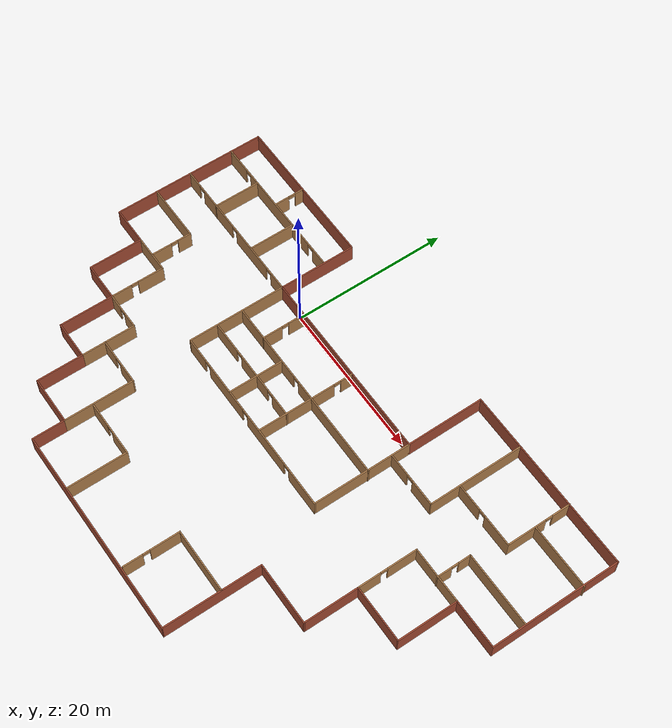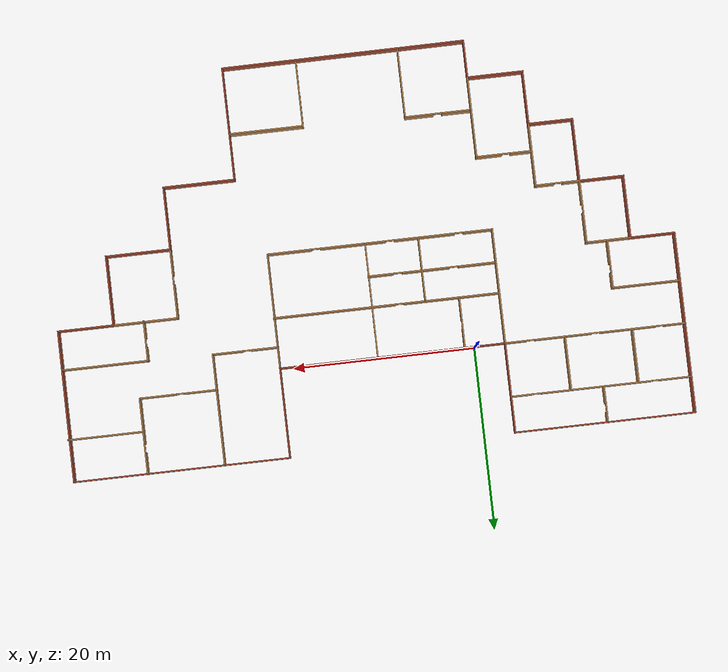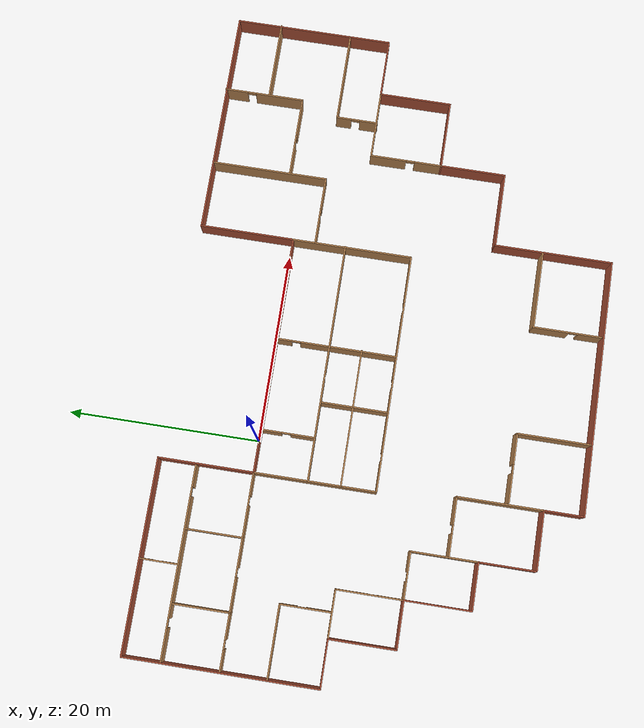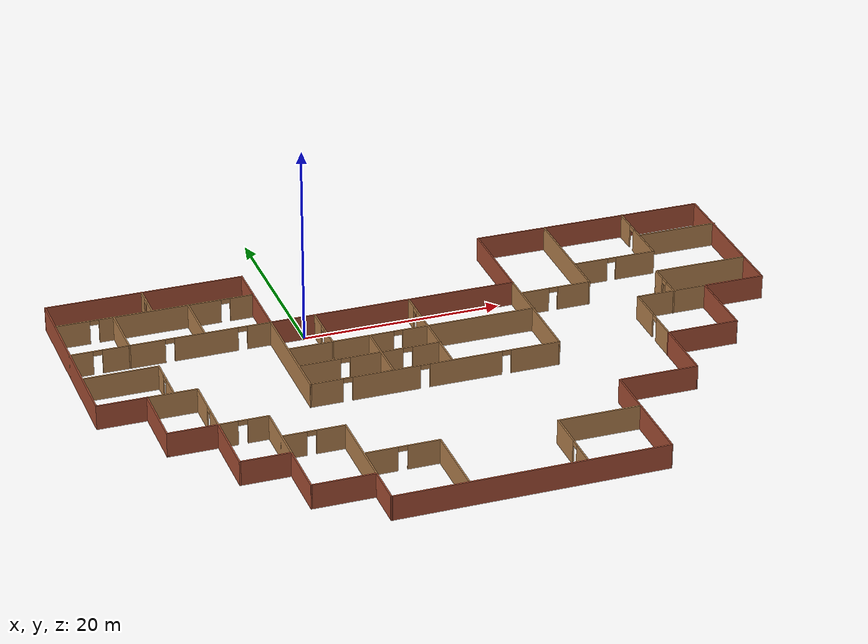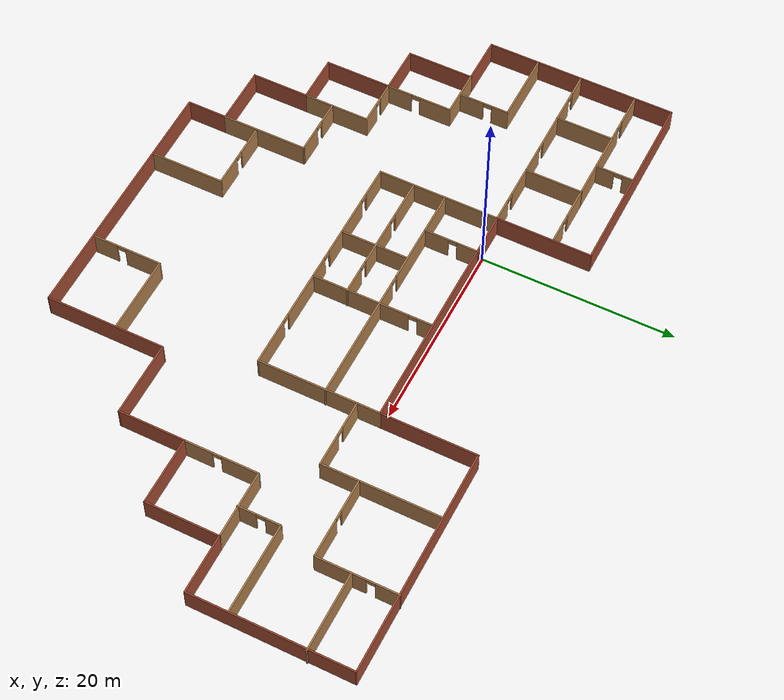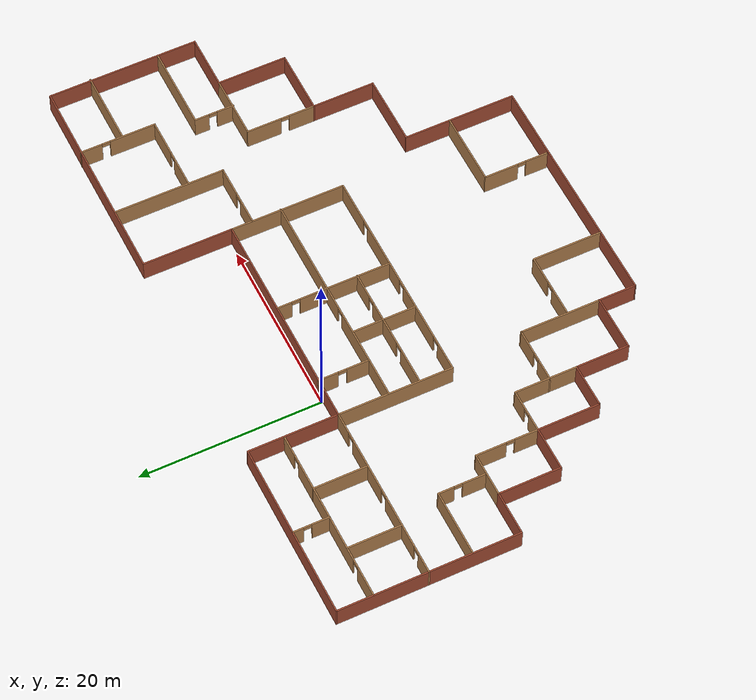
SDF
<?xml version='1.0'?>
<sdf version='1.6'>
  <model name='My_building'>
    <pose frame=''>11.044 -12.0312 0 0 -0 0</pose>
    <link name='Wall_104'>
      <collision name='Wall_104_Collision'>
        <geometry>
          <box>
            <size>7.25 0.15 2.5</size>
          </box>
        </geometry>
        <pose frame=''>0 0 1.25 0 -0 0</pose>
      </collision>
      <visual name='Wall_104_Visual'>
        <pose frame=''>0 0 1.25 0 -0 0</pose>
        <geometry>
          <box>
            <size>7.25 0.15 2.5</size>
          </box>
        </geometry>
        <material>
          <script>
            <uri>file://media/materials/scripts/gazebo.material</uri>
            <name>Gazebo/Bricks</name>
          </script>
          <ambient>0.333333 1 1 1</ambient>
        </material>
        <meta>
          <layer>0</layer>
        </meta>
      </visual>
      <pose frame=''>24.508 -2.47483 0 0 -0 0</pose>
    </link>
    <link name='Wall_105'>
      <collision name='Wall_105_Collision'>
        <geometry>
          <box>
            <size>7.75 0.15 2.5</size>
          </box>
        </geometry>
        <pose frame=''>0 0 1.25 0 -0 0</pose>
      </collision>
      <visual name='Wall_105_Visual'>
        <pose frame=''>0 0 1.25 0 -0 0</pose>
        <geometry>
          <box>
            <size>7.75 0.15 2.5</size>
          </box>
        </geometry>
        <material>
          <script>
            <uri>file://media/materials/scripts/gazebo.material</uri>
            <name>Gazebo/Bricks</name>
          </script>
          <ambient>0.333333 1 1 1</ambient>
        </material>
        <meta>
          <layer>0</layer>
        </meta>
      </visual>
      <pose frame=''>28.058 1.32517 0 0 -0 1.5708</pose>
    </link>
    <link name='Wall_106'>
      <collision name='Wall_106_Collision'>
        <geometry>
          <box>
            <size>6.25 0.15 2.5</size>
          </box>
        </geometry>
        <pose frame=''>0 0 1.25 0 -0 0</pose>
      </collision>
      <visual name='Wall_106_Visual'>
        <pose frame=''>0 0 1.25 0 -0 0</pose>
        <geometry>
          <box>
            <size>6.25 0.15 2.5</size>
          </box>
        </geometry>
        <material>
          <script>
            <uri>file://media/materials/scripts/gazebo.material</uri>
            <name>Gazebo/Bricks</name>
          </script>
          <ambient>0.333333 1 1 1</ambient>
        </material>
        <meta>
          <layer>0</layer>
        </meta>
      </visual>
      <pose frame=''>31.108 5.12517 0 0 -0 0</pose>
    </link>
    <link name='Wall_107'>
      <collision name='Wall_107_Collision'>
        <geometry>
          <box>
            <size>16.75 0.15 2.5</size>
          </box>
        </geometry>
        <pose frame=''>0 0 1.25 0 -0 0</pose>
      </collision>
      <visual name='Wall_107_Visual'>
        <pose frame=''>0 0 1.25 0 -0 0</pose>
        <geometry>
          <box>
            <size>16.75 0.15 2.5</size>
          </box>
        </geometry>
        <material>
          <script>
            <uri>file://media/materials/scripts/gazebo.material</uri>
            <name>Gazebo/Bricks</name>
          </script>
          <ambient>0.333333 1 1 1</ambient>
        </material>
        <meta>
          <layer>0</layer>
        </meta>
      </visual>
      <pose frame=''>34.158 13.4252 0 0 -0 1.5708</pose>
    </link>
    <link name='Wall_110'>
      <collision name='Wall_110_Collision'>
        <geometry>
          <box>
            <size>23.9 0.15 2.5</size>
          </box>
        </geometry>
        <pose frame=''>0 0 1.25 0 -0 0</pose>
      </collision>
      <visual name='Wall_110_Visual'>
        <pose frame=''>0 0 1.25 0 -0 0</pose>
        <geometry>
          <box>
            <size>23.9 0.15 2.5</size>
          </box>
        </geometry>
        <material>
          <script>
            <uri>file://media/materials/scripts/gazebo.material</uri>
            <name>Gazebo/Bricks</name>
          </script>
          <ambient>0.333333 1 1 1</ambient>
        </material>
        <meta>
          <layer>0</layer>
        </meta>
      </visual>
      <pose frame=''>22.283 21.7252 0 0 -0 0</pose>
    </link>
    <link name='Wall_112'>
      <collision name='Wall_112_Collision'>
        <geometry>
          <box>
            <size>12.75 0.15 2.5</size>
          </box>
        </geometry>
        <pose frame=''>0 0 1.25 0 -0 0</pose>
      </collision>
      <visual name='Wall_112_Visual'>
        <pose frame=''>0 0 1.25 0 -0 0</pose>
        <geometry>
          <box>
            <size>12.75 0.15 2.5</size>
          </box>
        </geometry>
        <material>
          <script>
            <uri>file://media/materials/scripts/gazebo.material</uri>
            <name>Gazebo/Wood</name>
          </script>
          <ambient>0.435294 0.796078 0.67451 1</ambient>
        </material>
        <meta>
          <layer>0</layer>
        </meta>
      </visual>
      <pose frame=''>-14.442 5.57517 0 0 0 -1.5708</pose>
    </link>
    <link name='Wall_115'>
      <collision name='Wall_115_Collision'>
        <geometry>
          <box>
            <size>12.75 0.15 2.5</size>
          </box>
        </geometry>
        <pose frame=''>0 0 1.25 0 -0 0</pose>
      </collision>
      <visual name='Wall_115_Visual'>
        <pose frame=''>0 0 1.25 0 -0 0</pose>
        <geometry>
          <box>
            <size>12.75 0.15 2.5</size>
          </box>
        </geometry>
        <material>
          <script>
            <uri>file://media/materials/scripts/gazebo.material</uri>
            <name>Gazebo/Wood</name>
          </script>
          <ambient>0.435294 0.796078 0.67451 1</ambient>
        </material>
        <meta>
          <layer>0</layer>
        </meta>
      </visual>
      <pose frame=''>10.408 5.57517 0 0 0 -1.5708</pose>
    </link>
    <link name='Wall_120'>
      <pose frame=''>-2.017 -0.724831 0 0 -0 0</pose>
      <visual name='Wall_120_Visual_0'>
        <pose frame=''>-10.8536 0 1.25 0 -0 0</pose>
        <geometry>
          <box>
            <size>3.29273 0.15 2.5</size>
          </box>
        </geometry>
        <material>
          <script>
            <uri>file://media/materials/scripts/gazebo.material</uri>
            <name>Gazebo/Wood</name>
          </script>
          <ambient>0.435294 0.796078 0.67451 1</ambient>
        </material>
        <meta>
          <layer>0</layer>
        </meta>
      </visual>
      <collision name='Wall_120_Collision_0'>
        <geometry>
          <box>
            <size>3.29273 0.15 2.5</size>
          </box>
        </geometry>
        <pose frame=''>-10.8536 0 1.25 0 -0 0</pose>
      </collision>
      <visual name='Wall_120_Visual_1'>
        <pose frame=''>-4.93656 0 1.25 0 -0 0</pose>
        <geometry>
          <box>
            <size>6.74143 0.15 2.5</size>
          </box>
        </geometry>
        <material>
          <script>
            <uri>file://media/materials/scripts/gazebo.material</uri>
            <name>Gazebo/Wood</name>
          </script>
          <ambient>0.435294 0.796078 0.67451 1</ambient>
        </material>
        <meta>
          <layer>0</layer>
        </meta>
      </visual>
      <collision name='Wall_120_Collision_1'>
        <geometry>
          <box>
            <size>6.74143 0.15 2.5</size>
          </box>
        </geometry>
        <pose frame=''>-4.93656 0 1.25 0 -0 0</pose>
      </collision>
      <visual name='Wall_120_Visual_2'>
        <pose frame=''>2.97536 0 1.25 0 -0 0</pose>
        <geometry>
          <box>
            <size>7.28242 0.15 2.5</size>
          </box>
        </geometry>
        <material>
          <script>
            <uri>file://media/materials/scripts/gazebo.material</uri>
            <name>Gazebo/Wood</name>
          </script>
          <ambient>0.435294 0.796078 0.67451 1</ambient>
        </material>
        <meta>
          <layer>0</layer>
        </meta>
      </visual>
      <collision name='Wall_120_Collision_2'>
        <geometry>
          <box>
            <size>7.28242 0.15 2.5</size>
          </box>
        </geometry>
        <pose frame=''>2.97536 0 1.25 0 -0 0</pose>
      </collision>
      <visual name='Wall_120_Visual_3'>
        <pose frame=''>10.0083 0 1.25 0 -0 0</pose>
        <geometry>
          <box>
            <size>4.98343 0.15 2.5</size>
          </box>
        </geometry>
        <material>
          <script>
            <uri>file://media/materials/scripts/gazebo.material</uri>
            <name>Gazebo/Wood</name>
          </script>
          <ambient>0.435294 0.796078 0.67451 1</ambient>
        </material>
        <meta>
          <layer>0</layer>
        </meta>
      </visual>
      <collision name='Wall_120_Collision_3'>
        <geometry>
          <box>
            <size>4.98343 0.15 2.5</size>
          </box>
        </geometry>
        <pose frame=''>10.0083 0 1.25 0 -0 0</pose>
      </collision>
      <visual name='Wall_120_Visual_4'>
        <pose frame=''>-8.75727 0 2.25 0 -0 0</pose>
        <geometry>
          <box>
            <size>0.9 0.15 0.5</size>
          </box>
        </geometry>
        <material>
          <script>
            <uri>file://media/materials/scripts/gazebo.material</uri>
            <name>Gazebo/Wood</name>
          </script>
          <ambient>0.435294 0.796078 0.67451 1</ambient>
        </material>
        <meta>
          <layer>0</layer>
        </meta>
      </visual>
      <collision name='Wall_120_Collision_4'>
        <geometry>
          <box>
            <size>0.9 0.15 0.5</size>
          </box>
        </geometry>
        <pose frame=''>-8.75727 0 2.25 0 -0 0</pose>
      </collision>
      <visual name='Wall_120_Visual_5'>
        <pose frame=''>-1.11584 0 2.25 0 -0 0</pose>
        <geometry>
          <box>
            <size>0.9 0.15 0.5</size>
          </box>
        </geometry>
        <material>
          <script>
            <uri>file://media/materials/scripts/gazebo.material</uri>
            <name>Gazebo/Wood</name>
          </script>
          <ambient>0.435294 0.796078 0.67451 1</ambient>
        </material>
        <meta>
          <layer>0</layer>
        </meta>
      </visual>
      <collision name='Wall_120_Collision_5'>
        <geometry>
          <box>
            <size>0.9 0.15 0.5</size>
          </box>
        </geometry>
        <pose frame=''>-1.11584 0 2.25 0 -0 0</pose>
      </collision>
      <visual name='Wall_120_Visual_6'>
        <pose frame=''>7.06657 0 2.25 0 -0 0</pose>
        <geometry>
          <box>
            <size>0.9 0.15 0.5</size>
          </box>
        </geometry>
        <material>
          <script>
            <uri>file://media/materials/scripts/gazebo.material</uri>
            <name>Gazebo/Wood</name>
          </script>
          <ambient>0.435294 0.796078 0.67451 1</ambient>
        </material>
        <meta>
          <layer>0</layer>
        </meta>
      </visual>
      <collision name='Wall_120_Collision_6'>
        <geometry>
          <box>
            <size>0.9 0.15 0.5</size>
          </box>
        </geometry>
        <pose frame=''>7.06657 0 2.25 0 -0 0</pose>
      </collision>
    </link>
    <link name='Wall_122'>
      <pose frame=''>-1.93956 6.30992 0 0 -0 0</pose>
      <visual name='Wall_122_Visual_0'>
        <pose frame=''>-7.21918 0 1.25 0 -0 0</pose>
        <geometry>
          <box>
            <size>10.5616 0.15 2.5</size>
          </box>
        </geometry>
        <material>
          <script>
            <uri>file://media/materials/scripts/gazebo.material</uri>
            <name>Gazebo/Wood</name>
          </script>
          <ambient>0.435294 0.796078 0.67451 1</ambient>
        </material>
        <meta>
          <layer>0</layer>
        </meta>
      </visual>
      <collision name='Wall_122_Collision_0'>
        <geometry>
          <box>
            <size>10.5616 0.15 2.5</size>
          </box>
        </geometry>
        <pose frame=''>-7.21918 0 1.25 0 -0 0</pose>
      </collision>
      <visual name='Wall_122_Visual_1'>
        <pose frame=''>5.73082 0 1.25 0 -0 0</pose>
        <geometry>
          <box>
            <size>13.5384 0.15 2.5</size>
          </box>
        </geometry>
        <material>
          <script>
            <uri>file://media/materials/scripts/gazebo.material</uri>
            <name>Gazebo/Wood</name>
          </script>
          <ambient>0.435294 0.796078 0.67451 1</ambient>
        </material>
        <meta>
          <layer>0</layer>
        </meta>
      </visual>
      <collision name='Wall_122_Collision_1'>
        <geometry>
          <box>
            <size>13.5384 0.15 2.5</size>
          </box>
        </geometry>
        <pose frame=''>5.73082 0 1.25 0 -0 0</pose>
      </collision>
      <visual name='Wall_122_Visual_2'>
        <pose frame=''>-1.48836 0 2.25 0 -0 0</pose>
        <geometry>
          <box>
            <size>0.9 0.15 0.5</size>
          </box>
        </geometry>
        <material>
          <script>
            <uri>file://media/materials/scripts/gazebo.material</uri>
            <name>Gazebo/Wood</name>
          </script>
          <ambient>0.435294 0.796078 0.67451 1</ambient>
        </material>
        <meta>
          <layer>0</layer>
        </meta>
      </visual>
      <collision name='Wall_122_Collision_2'>
        <geometry>
          <box>
            <size>0.9 0.15 0.5</size>
          </box>
        </geometry>
        <pose frame=''>-1.48836 0 2.25 0 -0 0</pose>
      </collision>
    </link>
    <link name='Wall_124'>
      <collision name='Wall_124_Collision'>
        <geometry>
          <box>
            <size>7 0.15 2.5</size>
          </box>
        </geometry>
        <pose frame=''>0 0 1.25 0 -0 0</pose>
      </collision>
      <visual name='Wall_124_Visual'>
        <pose frame=''>0 0 1.25 0 -0 0</pose>
        <geometry>
          <box>
            <size>7 0.15 2.5</size>
          </box>
        </geometry>
        <material>
          <script>
            <uri>file://media/materials/scripts/gazebo.material</uri>
            <name>Gazebo/Wood</name>
          </script>
          <ambient>0.435294 0.796078 0.67451 1</ambient>
        </material>
        <meta>
          <layer>0</layer>
        </meta>
      </visual>
      <pose frame=''>-0.391735 2.74657 0 0 0 -1.5708</pose>
    </link>
    <link name='Wall_126'>
      <collision name='Wall_126_Collision'>
        <geometry>
          <box>
            <size>7 0.15 2.5</size>
          </box>
        </geometry>
        <pose frame=''>0 0 1.25 0 -0 0</pose>
      </collision>
      <visual name='Wall_126_Visual'>
        <pose frame=''>0 0 1.25 0 -0 0</pose>
        <geometry>
          <box>
            <size>7 0.15 2.5</size>
          </box>
        </geometry>
        <material>
          <script>
            <uri>file://media/materials/scripts/gazebo.material</uri>
            <name>Gazebo/Wood</name>
          </script>
          <ambient>0.435294 0.796078 0.67451 1</ambient>
        </material>
        <meta>
          <layer>0</layer>
        </meta>
      </visual>
      <pose frame=''>-6.27139 2.81575 0 0 0 -1.5708</pose>
    </link>
    <link name='Wall_128'>
      <pose frame=''>-7.38373 2.92047 0 0 -0 0</pose>
      <visual name='Wall_128_Visual_0'>
        <pose frame=''>-5.00941 0 1.25 0 -0 0</pose>
        <geometry>
          <box>
            <size>4.23118 0.15 2.5</size>
          </box>
        </geometry>
        <material>
          <script>
            <uri>file://media/materials/scripts/gazebo.material</uri>
            <name>Gazebo/Wood</name>
          </script>
          <ambient>0.435294 0.796078 0.67451 1</ambient>
        </material>
        <meta>
          <layer>0</layer>
        </meta>
      </visual>
      <collision name='Wall_128_Collision_0'>
        <geometry>
          <box>
            <size>4.23118 0.15 2.5</size>
          </box>
        </geometry>
        <pose frame=''>-5.00941 0 1.25 0 -0 0</pose>
      </collision>
      <visual name='Wall_128_Visual_1'>
        <pose frame=''>0.666855 0 1.25 0 -0 0</pose>
        <geometry>
          <box>
            <size>5.32134 0.15 2.5</size>
          </box>
        </geometry>
        <material>
          <script>
            <uri>file://media/materials/scripts/gazebo.material</uri>
            <name>Gazebo/Wood</name>
          </script>
          <ambient>0.435294 0.796078 0.67451 1</ambient>
        </material>
        <meta>
          <layer>0</layer>
        </meta>
      </visual>
      <collision name='Wall_128_Collision_1'>
        <geometry>
          <box>
            <size>5.32134 0.15 2.5</size>
          </box>
        </geometry>
        <pose frame=''>0.666855 0 1.25 0 -0 0</pose>
      </collision>
      <visual name='Wall_128_Visual_2'>
        <pose frame=''>5.67626 0 1.25 0 -0 0</pose>
        <geometry>
          <box>
            <size>2.89748 0.15 2.5</size>
          </box>
        </geometry>
        <material>
          <script>
            <uri>file://media/materials/scripts/gazebo.material</uri>
            <name>Gazebo/Wood</name>
          </script>
          <ambient>0.435294 0.796078 0.67451 1</ambient>
        </material>
        <meta>
          <layer>0</layer>
        </meta>
      </visual>
      <collision name='Wall_128_Collision_2'>
        <geometry>
          <box>
            <size>2.89748 0.15 2.5</size>
          </box>
        </geometry>
        <pose frame=''>5.67626 0 1.25 0 -0 0</pose>
      </collision>
      <visual name='Wall_128_Visual_3'>
        <pose frame=''>-2.44382 0 2.25 0 -0 0</pose>
        <geometry>
          <box>
            <size>0.9 0.15 0.5</size>
          </box>
        </geometry>
        <material>
          <script>
            <uri>file://media/materials/scripts/gazebo.material</uri>
            <name>Gazebo/Wood</name>
          </script>
          <ambient>0.435294 0.796078 0.67451 1</ambient>
        </material>
        <meta>
          <layer>0</layer>
        </meta>
      </visual>
      <collision name='Wall_128_Collision_3'>
        <geometry>
          <box>
            <size>0.9 0.15 0.5</size>
          </box>
        </geometry>
        <pose frame=''>-2.44382 0 2.25 0 -0 0</pose>
      </collision>
      <visual name='Wall_128_Visual_4'>
        <pose frame=''>3.77752 0 2.25 0 -0 0</pose>
        <geometry>
          <box>
            <size>0.9 0.15 0.5</size>
          </box>
        </geometry>
        <material>
          <script>
            <uri>file://media/materials/scripts/gazebo.material</uri>
            <name>Gazebo/Wood</name>
          </script>
          <ambient>0.435294 0.796078 0.67451 1</ambient>
        </material>
        <meta>
          <layer>0</layer>
        </meta>
      </visual>
      <collision name='Wall_128_Collision_4'>
        <geometry>
          <box>
            <size>0.9 0.15 0.5</size>
          </box>
        </geometry>
        <pose frame=''>3.77752 0 2.25 0 -0 0</pose>
      </collision>
    </link>
    <link name='Wall_130'>
      <pose frame=''>-0.391735 9.12326 0 0 -0 1.5708</pose>
      <visual name='Wall_130_Visual_0'>
        <pose frame=''>-1.25641 0 1.25 0 -0 0</pose>
        <geometry>
          <box>
            <size>2.98718 0.15 2.5</size>
          </box>
        </geometry>
        <material>
          <script>
            <uri>file://media/materials/scripts/gazebo.material</uri>
            <name>Gazebo/Wood</name>
          </script>
          <ambient>0.435294 0.796078 0.67451 1</ambient>
        </material>
        <meta>
          <layer>0</layer>
        </meta>
      </visual>
      <collision name='Wall_130_Collision_0'>
        <geometry>
          <box>
            <size>2.98718 0.15 2.5</size>
          </box>
        </geometry>
        <pose frame=''>-1.25641 0 1.25 0 -0 0</pose>
      </collision>
      <visual name='Wall_130_Visual_1'>
        <pose frame=''>1.94359 0 1.25 0 -0 0</pose>
        <geometry>
          <box>
            <size>1.61282 0.15 2.5</size>
          </box>
        </geometry>
        <material>
          <script>
            <uri>file://media/materials/scripts/gazebo.material</uri>
            <name>Gazebo/Wood</name>
          </script>
          <ambient>0.435294 0.796078 0.67451 1</ambient>
        </material>
        <meta>
          <layer>0</layer>
        </meta>
      </visual>
      <collision name='Wall_130_Collision_1'>
        <geometry>
          <box>
            <size>1.61282 0.15 2.5</size>
          </box>
        </geometry>
        <pose frame=''>1.94359 0 1.25 0 -0 0</pose>
      </collision>
      <visual name='Wall_130_Visual_2'>
        <pose frame=''>0.687178 0 2.25 0 -0 0</pose>
        <geometry>
          <box>
            <size>0.9 0.15 0.5</size>
          </box>
        </geometry>
        <material>
          <script>
            <uri>file://media/materials/scripts/gazebo.material</uri>
            <name>Gazebo/Wood</name>
          </script>
          <ambient>0.435294 0.796078 0.67451 1</ambient>
        </material>
        <meta>
          <layer>0</layer>
        </meta>
      </visual>
      <collision name='Wall_130_Collision_2'>
        <geometry>
          <box>
            <size>0.9 0.15 0.5</size>
          </box>
        </geometry>
        <pose frame=''>0.687178 0 2.25 0 -0 0</pose>
      </collision>
    </link>
    <link name='Wall_134'>
      <pose frame=''>-9.99647 9.10326 0 0 0 -1.5708</pose>
      <visual name='Wall_134_Visual_0'>
        <pose frame=''>-1.74931 0 1.25 0 -0 0</pose>
        <geometry>
          <box>
            <size>2.25138 0.15 2.5</size>
          </box>
        </geometry>
        <material>
          <script>
            <uri>file://media/materials/scripts/gazebo.material</uri>
            <name>Gazebo/Wood</name>
          </script>
          <ambient>0.435294 0.796078 0.67451 1</ambient>
        </material>
        <meta>
          <layer>0</layer>
        </meta>
      </visual>
      <collision name='Wall_134_Collision_0'>
        <geometry>
          <box>
            <size>2.25138 0.15 2.5</size>
          </box>
        </geometry>
        <pose frame=''>-1.74931 0 1.25 0 -0 0</pose>
      </collision>
      <visual name='Wall_134_Visual_1'>
        <pose frame=''>1.57569 0 1.25 0 -0 0</pose>
        <geometry>
          <box>
            <size>2.59862 0.15 2.5</size>
          </box>
        </geometry>
        <material>
          <script>
            <uri>file://media/materials/scripts/gazebo.material</uri>
            <name>Gazebo/Wood</name>
          </script>
          <ambient>0.435294 0.796078 0.67451 1</ambient>
        </material>
        <meta>
          <layer>0</layer>
        </meta>
      </visual>
      <collision name='Wall_134_Collision_1'>
        <geometry>
          <box>
            <size>2.59862 0.15 2.5</size>
          </box>
        </geometry>
        <pose frame=''>1.57569 0 1.25 0 -0 0</pose>
      </collision>
      <visual name='Wall_134_Visual_2'>
        <pose frame=''>-0.17362 0 2.25 0 -0 0</pose>
        <geometry>
          <box>
            <size>0.9 0.15 0.5</size>
          </box>
        </geometry>
        <material>
          <script>
            <uri>file://media/materials/scripts/gazebo.material</uri>
            <name>Gazebo/Wood</name>
          </script>
          <ambient>0.435294 0.796078 0.67451 1</ambient>
        </material>
        <meta>
          <layer>0</layer>
        </meta>
      </visual>
      <collision name='Wall_134_Collision_2'>
        <geometry>
          <box>
            <size>0.9 0.15 0.5</size>
          </box>
        </geometry>
        <pose frame=''>-0.17362 0 2.25 0 -0 0</pose>
      </collision>
    </link>
    <link name='Wall_137'>
      <collision name='Wall_137_Collision'>
        <geometry>
          <box>
            <size>5 0.15 2.5</size>
          </box>
        </geometry>
        <pose frame=''>0 0 1.25 0 -0 0</pose>
      </collision>
      <visual name='Wall_137_Visual'>
        <pose frame=''>0 0 1.25 0 -0 0</pose>
        <geometry>
          <box>
            <size>5 0.15 2.5</size>
          </box>
        </geometry>
        <material>
          <script>
            <uri>file://media/materials/scripts/gazebo.material</uri>
            <name>Gazebo/Wood</name>
          </script>
          <ambient>1 1 0 1</ambient>
        </material>
        <meta>
          <layer>0</layer>
        </meta>
      </visual>
      <pose frame=''>-27.017 1.87517 0 0 -0 0</pose>
    </link>
    <link name='Wall_139'>
      <pose frame=''>-24.592 -1.54983 0 0 0 -1.5708</pose>
      <visual name='Wall_139_Visual_0'>
        <pose frame=''>-1.78358 0 1.25 0 -0 0</pose>
        <geometry>
          <box>
            <size>3.43283 0.15 2.5</size>
          </box>
        </geometry>
        <material>
          <script>
            <uri>file://media/materials/scripts/gazebo.material</uri>
            <name>Gazebo/Wood</name>
          </script>
          <ambient>1 1 0 1</ambient>
        </material>
        <meta>
          <layer>0</layer>
        </meta>
      </visual>
      <collision name='Wall_139_Collision_0'>
        <geometry>
          <box>
            <size>3.43283 0.15 2.5</size>
          </box>
        </geometry>
        <pose frame=''>-1.78358 0 1.25 0 -0 0</pose>
      </collision>
      <visual name='Wall_139_Visual_1'>
        <pose frame=''>2.16642 0 1.25 0 -0 0</pose>
        <geometry>
          <box>
            <size>2.66717 0.15 2.5</size>
          </box>
        </geometry>
        <material>
          <script>
            <uri>file://media/materials/scripts/gazebo.material</uri>
            <name>Gazebo/Wood</name>
          </script>
          <ambient>1 1 0 1</ambient>
        </material>
        <meta>
          <layer>0</layer>
        </meta>
      </visual>
      <collision name='Wall_139_Collision_1'>
        <geometry>
          <box>
            <size>2.66717 0.15 2.5</size>
          </box>
        </geometry>
        <pose frame=''>2.16642 0 1.25 0 -0 0</pose>
      </collision>
      <visual name='Wall_139_Visual_2'>
        <pose frame=''>0.382831 0 2.25 0 -0 0</pose>
        <geometry>
          <box>
            <size>0.9 0.15 0.5</size>
          </box>
        </geometry>
        <material>
          <script>
            <uri>file://media/materials/scripts/gazebo.material</uri>
            <name>Gazebo/Wood</name>
          </script>
          <ambient>1 1 0 1</ambient>
        </material>
        <meta>
          <layer>0</layer>
        </meta>
      </visual>
      <collision name='Wall_139_Collision_2'>
        <geometry>
          <box>
            <size>0.9 0.15 0.5</size>
          </box>
        </geometry>
        <pose frame=''>0.382831 0 2.25 0 -0 0</pose>
      </collision>
    </link>
    <link name='Wall_143'>
      <pose frame=''>-22.167 -4.97483 0 0 -0 0</pose>
      <visual name='Wall_143_Visual_0'>
        <pose frame=''>-1.52696 0 1.25 0 -0 0</pose>
        <geometry>
          <box>
            <size>1.94607 0.15 2.5</size>
          </box>
        </geometry>
        <material>
          <script>
            <uri>file://media/materials/scripts/gazebo.material</uri>
            <name>Gazebo/Wood</name>
          </script>
          <ambient>1 1 0 1</ambient>
        </material>
        <meta>
          <layer>0</layer>
        </meta>
      </visual>
      <collision name='Wall_143_Collision_0'>
        <geometry>
          <box>
            <size>1.94607 0.15 2.5</size>
          </box>
        </geometry>
        <pose frame=''>-1.52696 0 1.25 0 -0 0</pose>
      </collision>
      <visual name='Wall_143_Visual_1'>
        <pose frame=''>1.42304 0 1.25 0 -0 0</pose>
        <geometry>
          <box>
            <size>2.15393 0.15 2.5</size>
          </box>
        </geometry>
        <material>
          <script>
            <uri>file://media/materials/scripts/gazebo.material</uri>
            <name>Gazebo/Wood</name>
          </script>
          <ambient>1 1 0 1</ambient>
        </material>
        <meta>
          <layer>0</layer>
        </meta>
      </visual>
      <collision name='Wall_143_Collision_1'>
        <geometry>
          <box>
            <size>2.15393 0.15 2.5</size>
          </box>
        </geometry>
        <pose frame=''>1.42304 0 1.25 0 -0 0</pose>
      </collision>
      <visual name='Wall_143_Visual_2'>
        <pose frame=''>-0.10393 0 2.25 0 -0 0</pose>
        <geometry>
          <box>
            <size>0.9 0.15 0.5</size>
          </box>
        </geometry>
        <material>
          <script>
            <uri>file://media/materials/scripts/gazebo.material</uri>
            <name>Gazebo/Wood</name>
          </script>
          <ambient>1 1 0 1</ambient>
        </material>
        <meta>
          <layer>0</layer>
        </meta>
      </visual>
      <collision name='Wall_143_Collision_2'>
        <geometry>
          <box>
            <size>0.9 0.15 0.5</size>
          </box>
        </geometry>
        <pose frame=''>-0.10393 0 2.25 0 -0 0</pose>
      </collision>
    </link>
    <link name='Wall_145'>
      <collision name='Wall_145_Collision'>
        <geometry>
          <box>
            <size>7 0.15 2.5</size>
          </box>
        </geometry>
        <pose frame=''>0 0 1.25 0 -0 0</pose>
      </collision>
      <visual name='Wall_145_Visual'>
        <pose frame=''>0 0 1.25 0 -0 0</pose>
        <geometry>
          <box>
            <size>7 0.15 2.5</size>
          </box>
        </geometry>
        <material>
          <script>
            <uri>file://media/materials/scripts/gazebo.material</uri>
            <name>Gazebo/Wood</name>
          </script>
          <ambient>1 1 0 1</ambient>
        </material>
        <meta>
          <layer>0</layer>
        </meta>
      </visual>
      <pose frame=''>-19.742 -8.39983 0 0 0 -1.5708</pose>
    </link>
    <link name='Wall_151'>
      <collision name='Wall_151_Collision'>
        <geometry>
          <box>
            <size>5 0.15 2.5</size>
          </box>
        </geometry>
        <pose frame=''>0 0 1.25 0 -0 0</pose>
      </collision>
      <visual name='Wall_151_Visual'>
        <pose frame=''>0 0 1.25 0 -0 0</pose>
        <geometry>
          <box>
            <size>5 0.15 2.5</size>
          </box>
        </geometry>
        <material>
          <script>
            <uri>file://media/materials/scripts/gazebo.material</uri>
            <name>Gazebo/Bricks</name>
          </script>
          <ambient>0.333333 1 1 1</ambient>
        </material>
        <meta>
          <layer>0</layer>
        </meta>
      </visual>
      <pose frame=''>-22.167 -11.8248 0 0 -0 0</pose>
    </link>
    <link name='Wall_152'>
      <collision name='Wall_152_Collision'>
        <geometry>
          <box>
            <size>6 0.15 2.5</size>
          </box>
        </geometry>
        <pose frame=''>0 0 1.25 0 -0 0</pose>
      </collision>
      <visual name='Wall_152_Visual'>
        <pose frame=''>0 0 1.25 0 -0 0</pose>
        <geometry>
          <box>
            <size>6 0.15 2.5</size>
          </box>
        </geometry>
        <material>
          <script>
            <uri>file://media/materials/scripts/gazebo.material</uri>
            <name>Gazebo/Bricks</name>
          </script>
          <ambient>0.333333 1 1 1</ambient>
        </material>
        <meta>
          <layer>0</layer>
        </meta>
      </visual>
      <pose frame=''>-19.742 -14.7498 0 0 0 -1.5708</pose>
    </link>
    <link name='Wall_153'>
      <collision name='Wall_153_Collision'>
        <geometry>
          <box>
            <size>6.25 0.15 2.5</size>
          </box>
        </geometry>
        <pose frame=''>0 0 1.25 0 -0 0</pose>
      </collision>
      <visual name='Wall_153_Visual'>
        <pose frame=''>0 0 1.25 0 -0 0</pose>
        <geometry>
          <box>
            <size>6.25 0.15 2.5</size>
          </box>
        </geometry>
        <material>
          <script>
            <uri>file://media/materials/scripts/gazebo.material</uri>
            <name>Gazebo/Bricks</name>
          </script>
          <ambient>0.333333 1 1 1</ambient>
        </material>
        <meta>
          <layer>0</layer>
        </meta>
      </visual>
      <pose frame=''>-16.692 -17.6748 0 0 -0 0</pose>
    </link>
    <link name='Wall_154'>
      <collision name='Wall_154_Collision'>
        <geometry>
          <box>
            <size>4.25 0.15 2.5</size>
          </box>
        </geometry>
        <pose frame=''>0 0 1.25 0 -0 0</pose>
      </collision>
      <visual name='Wall_154_Visual'>
        <pose frame=''>0 0 1.25 0 -0 0</pose>
        <geometry>
          <box>
            <size>4.25 0.15 2.5</size>
          </box>
        </geometry>
        <material>
          <script>
            <uri>file://media/materials/scripts/gazebo.material</uri>
            <name>Gazebo/Bricks</name>
          </script>
          <ambient>0.333333 1 1 1</ambient>
        </material>
        <meta>
          <layer>0</layer>
        </meta>
      </visual>
      <pose frame=''>-13.642 -19.7248 0 0 0 -1.5708</pose>
    </link>
    <link name='Wall_175'>
      <collision name='Wall_175_Collision'>
        <geometry>
          <box>
            <size>9 0.15 2.5</size>
          </box>
        </geometry>
        <pose frame=''>0 0 1.25 0 -0 0</pose>
      </collision>
      <visual name='Wall_175_Visual'>
        <pose frame=''>0 0 1.25 0 -0 0</pose>
        <geometry>
          <box>
            <size>9 0.15 2.5</size>
          </box>
        </geometry>
        <material>
          <script>
            <uri>file://media/materials/scripts/gazebo.material</uri>
            <name>Gazebo/Wood</name>
          </script>
          <ambient>1 1 0 1</ambient>
        </material>
        <meta>
          <layer>0</layer>
        </meta>
      </visual>
      <pose frame=''>-13.642 -13.2498 0 0 -0 1.5708</pose>
    </link>
    <link name='Wall_176'>
      <pose frame=''>-16.692 -8.82483 0 0 -0 3.14159</pose>
      <visual name='Wall_176_Visual_0'>
        <pose frame=''>-1.68139 0 1.25 0 -0 0</pose>
        <geometry>
          <box>
            <size>2.88721 0.15 2.5</size>
          </box>
        </geometry>
        <material>
          <script>
            <uri>file://media/materials/scripts/gazebo.material</uri>
            <name>Gazebo/Wood</name>
          </script>
          <ambient>1 1 0 1</ambient>
        </material>
        <meta>
          <layer>0</layer>
        </meta>
      </visual>
      <collision name='Wall_176_Collision_0'>
        <geometry>
          <box>
            <size>2.88721 0.15 2.5</size>
          </box>
        </geometry>
        <pose frame=''>-1.68139 0 1.25 0 -0 0</pose>
      </collision>
      <visual name='Wall_176_Visual_1'>
        <pose frame=''>1.89361 0 1.25 0 -0 0</pose>
        <geometry>
          <box>
            <size>2.46279 0.15 2.5</size>
          </box>
        </geometry>
        <material>
          <script>
            <uri>file://media/materials/scripts/gazebo.material</uri>
            <name>Gazebo/Wood</name>
          </script>
          <ambient>1 1 0 1</ambient>
        </material>
        <meta>
          <layer>0</layer>
        </meta>
      </visual>
      <collision name='Wall_176_Collision_1'>
        <geometry>
          <box>
            <size>2.46279 0.15 2.5</size>
          </box>
        </geometry>
        <pose frame=''>1.89361 0 1.25 0 -0 0</pose>
      </collision>
      <visual name='Wall_176_Visual_2'>
        <pose frame=''>0.212214 0 2.25 0 -0 0</pose>
        <geometry>
          <box>
            <size>0.9 0.15 0.5</size>
          </box>
        </geometry>
        <material>
          <script>
            <uri>file://media/materials/scripts/gazebo.material</uri>
            <name>Gazebo/Wood</name>
          </script>
          <ambient>1 1 0 1</ambient>
        </material>
        <meta>
          <layer>0</layer>
        </meta>
      </visual>
      <collision name='Wall_176_Collision_2'>
        <geometry>
          <box>
            <size>0.9 0.15 0.5</size>
          </box>
        </geometry>
        <pose frame=''>0.212214 0 2.25 0 -0 0</pose>
      </collision>
    </link>
    <link name='Wall_183'>
      <collision name='Wall_183_Collision'>
        <geometry>
          <box>
            <size>26.9002 0.15 2.5</size>
          </box>
        </geometry>
        <pose frame=''>0 0 1.25 0 -0 0</pose>
      </collision>
      <visual name='Wall_183_Visual'>
        <pose frame=''>0 0 1.25 0 -0 0</pose>
        <geometry>
          <box>
            <size>26.9002 0.15 2.5</size>
          </box>
        </geometry>
        <material>
          <script>
            <uri>file://media/materials/scripts/gazebo.material</uri>
            <name>Gazebo/Bricks</name>
          </script>
          <ambient>0.333333 1 1 1</ambient>
        </material>
        <meta>
          <layer>0</layer>
        </meta>
      </visual>
      <pose frame=''>-0.267003 -21.7248 0 0 -0 0.003738</pose>
    </link>
    <link name='Wall_185'>
      <pose frame=''>-9.87539 -14.0695 0 0 -0 0</pose>
      <visual name='Wall_185_Visual_0'>
        <pose frame=''>-2.06665 0 1.25 0 -0 0</pose>
        <geometry>
          <box>
            <size>3.1167 0.15 2.5</size>
          </box>
        </geometry>
        <material>
          <script>
            <uri>file://media/materials/scripts/gazebo.material</uri>
            <name>Gazebo/Wood</name>
          </script>
          <ambient>0.760784 0.662745 0.627451 1</ambient>
        </material>
        <meta>
          <layer>0</layer>
        </meta>
      </visual>
      <collision name='Wall_185_Collision_0'>
        <geometry>
          <box>
            <size>3.1167 0.15 2.5</size>
          </box>
        </geometry>
        <pose frame=''>-2.06665 0 1.25 0 -0 0</pose>
      </collision>
      <visual name='Wall_185_Visual_1'>
        <pose frame=''>2.00835 0 1.25 0 -0 0</pose>
        <geometry>
          <box>
            <size>3.2333 0.15 2.5</size>
          </box>
        </geometry>
        <material>
          <script>
            <uri>file://media/materials/scripts/gazebo.material</uri>
            <name>Gazebo/Wood</name>
          </script>
          <ambient>0.760784 0.662745 0.627451 1</ambient>
        </material>
        <meta>
          <layer>0</layer>
        </meta>
      </visual>
      <collision name='Wall_185_Collision_1'>
        <geometry>
          <box>
            <size>3.2333 0.15 2.5</size>
          </box>
        </geometry>
        <pose frame=''>2.00835 0 1.25 0 -0 0</pose>
      </collision>
      <visual name='Wall_185_Visual_2'>
        <pose frame=''>-0.058299 0 2.25 0 -0 0</pose>
        <geometry>
          <box>
            <size>0.9 0.15 0.5</size>
          </box>
        </geometry>
        <material>
          <script>
            <uri>file://media/materials/scripts/gazebo.material</uri>
            <name>Gazebo/Wood</name>
          </script>
          <ambient>0.760784 0.662745 0.627451 1</ambient>
        </material>
        <meta>
          <layer>0</layer>
        </meta>
      </visual>
      <collision name='Wall_185_Collision_2'>
        <geometry>
          <box>
            <size>0.9 0.15 0.5</size>
          </box>
        </geometry>
        <pose frame=''>-0.058299 0 2.25 0 -0 0</pose>
      </collision>
    </link>
    <link name='Wall_186'>
      <collision name='Wall_186_Collision'>
        <geometry>
          <box>
            <size>7.75 0.15 2.5</size>
          </box>
        </geometry>
        <pose frame=''>0 0 1.25 0 -0 0</pose>
      </collision>
      <visual name='Wall_186_Visual'>
        <pose frame=''>0 0 1.25 0 -0 0</pose>
        <geometry>
          <box>
            <size>7.75 0.15 2.5</size>
          </box>
        </geometry>
        <material>
          <script>
            <uri>file://media/materials/scripts/gazebo.material</uri>
            <name>Gazebo/Wood</name>
          </script>
          <ambient>0.760784 0.662745 0.627451 1</ambient>
        </material>
        <meta>
          <layer>0</layer>
        </meta>
      </visual>
      <pose frame=''>-6.32539 -17.8695 0 0 0 -1.5708</pose>
    </link>
    <link name='Wall_190'>
      <pose frame=''>20.958 1.32517 0 0 -0 1.5708</pose>
      <visual name='Wall_190_Visual_0'>
        <pose frame=''>-2.39061 0 1.25 0 -0 0</pose>
        <geometry>
          <box>
            <size>2.96878 0.15 2.5</size>
          </box>
        </geometry>
        <material>
          <script>
            <uri>file://media/materials/scripts/gazebo.material</uri>
            <name>Gazebo/Wood</name>
          </script>
          <ambient>1 1 0 1</ambient>
        </material>
        <meta>
          <layer>0</layer>
        </meta>
      </visual>
      <collision name='Wall_190_Collision_0'>
        <geometry>
          <box>
            <size>2.96878 0.15 2.5</size>
          </box>
        </geometry>
        <pose frame=''>-2.39061 0 1.25 0 -0 0</pose>
      </collision>
      <visual name='Wall_190_Visual_1'>
        <pose frame=''>1.93439 0 1.25 0 -0 0</pose>
        <geometry>
          <box>
            <size>3.88122 0.15 2.5</size>
          </box>
        </geometry>
        <material>
          <script>
            <uri>file://media/materials/scripts/gazebo.material</uri>
            <name>Gazebo/Wood</name>
          </script>
          <ambient>1 1 0 1</ambient>
        </material>
        <meta>
          <layer>0</layer>
        </meta>
      </visual>
      <collision name='Wall_190_Collision_1'>
        <geometry>
          <box>
            <size>3.88122 0.15 2.5</size>
          </box>
        </geometry>
        <pose frame=''>1.93439 0 1.25 0 -0 0</pose>
      </collision>
      <visual name='Wall_190_Visual_2'>
        <pose frame=''>-0.456219 0 2.25 0 -0 0</pose>
        <geometry>
          <box>
            <size>0.9 0.15 0.5</size>
          </box>
        </geometry>
        <material>
          <script>
            <uri>file://media/materials/scripts/gazebo.material</uri>
            <name>Gazebo/Wood</name>
          </script>
          <ambient>1 1 0 1</ambient>
        </material>
        <meta>
          <layer>0</layer>
        </meta>
      </visual>
      <collision name='Wall_190_Collision_2'>
        <geometry>
          <box>
            <size>0.9 0.15 0.5</size>
          </box>
        </geometry>
        <pose frame=''>-0.456219 0 2.25 0 -0 0</pose>
      </collision>
    </link>
    <link name='Wall_192'>
      <collision name='Wall_192_Collision'>
        <geometry>
          <box>
            <size>7.25 0.15 2.5</size>
          </box>
        </geometry>
        <pose frame=''>0 0 1.25 0 -0 0</pose>
      </collision>
      <visual name='Wall_192_Visual'>
        <pose frame=''>0 0 1.25 0 -0 0</pose>
        <geometry>
          <box>
            <size>7.25 0.15 2.5</size>
          </box>
        </geometry>
        <material>
          <script>
            <uri>file://media/materials/scripts/gazebo.material</uri>
            <name>Gazebo/Wood</name>
          </script>
          <ambient>1 1 0 1</ambient>
        </material>
        <meta>
          <layer>0</layer>
        </meta>
      </visual>
      <pose frame=''>24.508 5.12517 0 0 -0 0</pose>
    </link>
    <link name='Wall_196'>
      <pose frame=''>4.97312 -17.9193 0 0 -0 1.5708</pose>
      <visual name='Wall_196_Visual_0'>
        <pose frame=''>-2.36842 0 1.25 0 -0 0</pose>
        <geometry>
          <box>
            <size>2.51317 0.15 2.5</size>
          </box>
        </geometry>
        <material>
          <script>
            <uri>file://media/materials/scripts/gazebo.material</uri>
            <name>Gazebo/Wood</name>
          </script>
          <ambient>0.760784 0.662745 0.627451 1</ambient>
        </material>
        <meta>
          <layer>0</layer>
        </meta>
      </visual>
      <collision name='Wall_196_Collision_0'>
        <geometry>
          <box>
            <size>2.51317 0.15 2.5</size>
          </box>
        </geometry>
        <pose frame=''>-2.36842 0 1.25 0 -0 0</pose>
      </collision>
      <visual name='Wall_196_Visual_1'>
        <pose frame=''>1.70659 0 1.25 0 -0 0</pose>
        <geometry>
          <box>
            <size>3.83683 0.15 2.5</size>
          </box>
        </geometry>
        <material>
          <script>
            <uri>file://media/materials/scripts/gazebo.material</uri>
            <name>Gazebo/Wood</name>
          </script>
          <ambient>0.760784 0.662745 0.627451 1</ambient>
        </material>
        <meta>
          <layer>0</layer>
        </meta>
      </visual>
      <collision name='Wall_196_Collision_1'>
        <geometry>
          <box>
            <size>3.83683 0.15 2.5</size>
          </box>
        </geometry>
        <pose frame=''>1.70659 0 1.25 0 -0 0</pose>
      </collision>
      <visual name='Wall_196_Visual_2'>
        <pose frame=''>-0.661831 0 2.25 0 -0 0</pose>
        <geometry>
          <box>
            <size>0.9 0.15 0.5</size>
          </box>
        </geometry>
        <material>
          <script>
            <uri>file://media/materials/scripts/gazebo.material</uri>
            <name>Gazebo/Wood</name>
          </script>
          <ambient>0.760784 0.662745 0.627451 1</ambient>
        </material>
        <meta>
          <layer>0</layer>
        </meta>
      </visual>
      <collision name='Wall_196_Collision_2'>
        <geometry>
          <box>
            <size>0.9 0.15 0.5</size>
          </box>
        </geometry>
        <pose frame=''>-0.661831 0 2.25 0 -0 0</pose>
      </collision>
    </link>
    <link name='Wall_197'>
      <collision name='Wall_197_Collision'>
        <geometry>
          <box>
            <size>8.25 0.15 2.5</size>
          </box>
        </geometry>
        <pose frame=''>0 0 1.25 0 -0 0</pose>
      </collision>
      <visual name='Wall_197_Visual'>
        <pose frame=''>0 0 1.25 0 -0 0</pose>
        <geometry>
          <box>
            <size>8.25 0.15 2.5</size>
          </box>
        </geometry>
        <material>
          <script>
            <uri>file://media/materials/scripts/gazebo.material</uri>
            <name>Gazebo/Wood</name>
          </script>
          <ambient>0.760784 0.662745 0.627451 1</ambient>
        </material>
        <meta>
          <layer>0</layer>
        </meta>
      </visual>
      <pose frame=''>9.02312 -14.3693 0 0 -0 0</pose>
    </link>
    <link name='Wall_200'>
      <collision name='Wall_200_Collision'>
        <geometry>
          <box>
            <size>12.5 0.15 2.5</size>
          </box>
        </geometry>
        <pose frame=''>0 0 1.25 0 -0 0</pose>
      </collision>
      <visual name='Wall_200_Visual'>
        <pose frame=''>0 0 1.25 0 -0 0</pose>
        <geometry>
          <box>
            <size>12.5 0.15 2.5</size>
          </box>
        </geometry>
        <material>
          <script>
            <uri>file://media/materials/scripts/gazebo.material</uri>
            <name>Gazebo/Bricks</name>
          </script>
          <ambient>0.333333 1 1 1</ambient>
        </material>
        <meta>
          <layer>0</layer>
        </meta>
      </visual>
      <pose frame=''>13.108 -15.4998 0 0 -0 1.5708</pose>
    </link>
    <link name='Wall_205'>
      <collision name='Wall_205_Collision'>
        <geometry>
          <box>
            <size>7 0.15 2.5</size>
          </box>
        </geometry>
        <pose frame=''>0 0 1.25 0 -0 0</pose>
      </collision>
      <visual name='Wall_205_Visual'>
        <pose frame=''>0 0 1.25 0 -0 0</pose>
        <geometry>
          <box>
            <size>7 0.15 2.5</size>
          </box>
        </geometry>
        <material>
          <script>
            <uri>file://media/materials/scripts/gazebo.material</uri>
            <name>Gazebo/Bricks</name>
          </script>
          <ambient>0.333333 1 1 1</ambient>
        </material>
        <meta>
          <layer>0</layer>
        </meta>
      </visual>
      <pose frame=''>20.958 -5.89983 0 0 0 -1.5708</pose>
    </link>
    <link name='Wall_207'>
      <collision name='Wall_207_Collision'>
        <geometry>
          <box>
            <size>8 0.15 2.5</size>
          </box>
        </geometry>
        <pose frame=''>0 0 1.25 0 -0 0</pose>
      </collision>
      <visual name='Wall_207_Visual'>
        <pose frame=''>0 0 1.25 0 -0 0</pose>
        <geometry>
          <box>
            <size>8 0.15 2.5</size>
          </box>
        </geometry>
        <material>
          <script>
            <uri>file://media/materials/scripts/gazebo.material</uri>
            <name>Gazebo/Bricks</name>
          </script>
          <ambient>0.333333 1 1 1</ambient>
        </material>
        <meta>
          <layer>0</layer>
        </meta>
      </visual>
      <pose frame=''>17.033 -9.32483 0 0 -0 0</pose>
    </link>
    <link name='Wall_209'>
      <pose frame=''>-24.367 11.8752 0 0 -0 3.14159</pose>
      <visual name='Wall_209_Visual_0'>
        <pose frame=''>-8.7635 0 1.25 0 -0 0</pose>
        <geometry>
          <box>
            <size>2.47301 0.15 2.5</size>
          </box>
        </geometry>
        <material>
          <script>
            <uri>file://media/materials/scripts/gazebo.material</uri>
            <name>Gazebo/Wood</name>
          </script>
          <ambient>0.996078 0.47451 0.0196078 1</ambient>
        </material>
        <meta>
          <layer>0</layer>
        </meta>
      </visual>
      <collision name='Wall_209_Collision_0'>
        <geometry>
          <box>
            <size>2.47301 0.15 2.5</size>
          </box>
        </geometry>
        <pose frame=''>-8.7635 0 1.25 0 -0 0</pose>
      </collision>
      <visual name='Wall_209_Visual_1'>
        <pose frame=''>-3.46084 0 1.25 0 -0 0</pose>
        <geometry>
          <box>
            <size>6.33231 0.15 2.5</size>
          </box>
        </geometry>
        <material>
          <script>
            <uri>file://media/materials/scripts/gazebo.material</uri>
            <name>Gazebo/Wood</name>
          </script>
          <ambient>0.996078 0.47451 0.0196078 1</ambient>
        </material>
        <meta>
          <layer>0</layer>
        </meta>
      </visual>
      <collision name='Wall_209_Collision_1'>
        <geometry>
          <box>
            <size>6.33231 0.15 2.5</size>
          </box>
        </geometry>
        <pose frame=''>-3.46084 0 1.25 0 -0 0</pose>
      </collision>
      <visual name='Wall_209_Visual_2'>
        <pose frame=''>3.69371 0 1.25 0 -0 0</pose>
        <geometry>
          <box>
            <size>6.17677 0.15 2.5</size>
          </box>
        </geometry>
        <material>
          <script>
            <uri>file://media/materials/scripts/gazebo.material</uri>
            <name>Gazebo/Wood</name>
          </script>
          <ambient>0.996078 0.47451 0.0196078 1</ambient>
        </material>
        <meta>
          <layer>0</layer>
        </meta>
      </visual>
      <collision name='Wall_209_Collision_2'>
        <geometry>
          <box>
            <size>6.17677 0.15 2.5</size>
          </box>
        </geometry>
        <pose frame=''>3.69371 0 1.25 0 -0 0</pose>
      </collision>
      <visual name='Wall_209_Visual_3'>
        <pose frame=''>8.84105 0 1.25 0 -0 0</pose>
        <geometry>
          <box>
            <size>2.31791 0.15 2.5</size>
          </box>
        </geometry>
        <material>
          <script>
            <uri>file://media/materials/scripts/gazebo.material</uri>
            <name>Gazebo/Wood</name>
          </script>
          <ambient>0.996078 0.47451 0.0196078 1</ambient>
        </material>
        <meta>
          <layer>0</layer>
        </meta>
      </visual>
      <collision name='Wall_209_Collision_3'>
        <geometry>
          <box>
            <size>2.31791 0.15 2.5</size>
          </box>
        </geometry>
        <pose frame=''>8.84105 0 1.25 0 -0 0</pose>
      </collision>
      <visual name='Wall_209_Visual_4'>
        <pose frame=''>-7.07699 0 2.25 0 -0 0</pose>
        <geometry>
          <box>
            <size>0.9 0.15 0.5</size>
          </box>
        </geometry>
        <material>
          <script>
            <uri>file://media/materials/scripts/gazebo.material</uri>
            <name>Gazebo/Wood</name>
          </script>
          <ambient>0.996078 0.47451 0.0196078 1</ambient>
        </material>
        <meta>
          <layer>0</layer>
        </meta>
      </visual>
      <collision name='Wall_209_Collision_4'>
        <geometry>
          <box>
            <size>0.9 0.15 0.5</size>
          </box>
        </geometry>
        <pose frame=''>-7.07699 0 2.25 0 -0 0</pose>
      </collision>
      <visual name='Wall_209_Visual_5'>
        <pose frame=''>0.155318 0 2.25 0 -0 0</pose>
        <geometry>
          <box>
            <size>0.9 0.15 0.5</size>
          </box>
        </geometry>
        <material>
          <script>
            <uri>file://media/materials/scripts/gazebo.material</uri>
            <name>Gazebo/Wood</name>
          </script>
          <ambient>0.996078 0.47451 0.0196078 1</ambient>
        </material>
        <meta>
          <layer>0</layer>
        </meta>
      </visual>
      <collision name='Wall_209_Collision_5'>
        <geometry>
          <box>
            <size>0.9 0.15 0.5</size>
          </box>
        </geometry>
        <pose frame=''>0.155318 0 2.25 0 -0 0</pose>
      </collision>
      <visual name='Wall_209_Visual_6'>
        <pose frame=''>7.23209 0 2.25 0 -0 0</pose>
        <geometry>
          <box>
            <size>0.9 0.15 0.5</size>
          </box>
        </geometry>
        <material>
          <script>
            <uri>file://media/materials/scripts/gazebo.material</uri>
            <name>Gazebo/Wood</name>
          </script>
          <ambient>0.996078 0.47451 0.0196078 1</ambient>
        </material>
        <meta>
          <layer>0</layer>
        </meta>
      </visual>
      <collision name='Wall_209_Collision_6'>
        <geometry>
          <box>
            <size>0.9 0.15 0.5</size>
          </box>
        </geometry>
        <pose frame=''>7.23209 0 2.25 0 -0 0</pose>
      </collision>
    </link>
    <link name='Wall_211'>
      <pose frame=''>-24.4385 17.778 0 0 -0 0</pose>
      <visual name='Wall_211_Visual_0'>
        <pose frame=''>-8.15955 0 1.25 0 -0 0</pose>
        <geometry>
          <box>
            <size>3.43091 0.15 2.5</size>
          </box>
        </geometry>
        <material>
          <script>
            <uri>file://media/materials/scripts/gazebo.material</uri>
            <name>Gazebo/Wood</name>
          </script>
          <ambient>0.996078 0.47451 0.0196078 1</ambient>
        </material>
        <meta>
          <layer>0</layer>
        </meta>
      </visual>
      <collision name='Wall_211_Collision_0'>
        <geometry>
          <box>
            <size>3.43091 0.15 2.5</size>
          </box>
        </geometry>
        <pose frame=''>-8.15955 0 1.25 0 -0 0</pose>
      </collision>
      <visual name='Wall_211_Visual_1'>
        <pose frame=''>0.577197 0 1.25 0 -0 0</pose>
        <geometry>
          <box>
            <size>12.2426 0.15 2.5</size>
          </box>
        </geometry>
        <material>
          <script>
            <uri>file://media/materials/scripts/gazebo.material</uri>
            <name>Gazebo/Wood</name>
          </script>
          <ambient>0.996078 0.47451 0.0196078 1</ambient>
        </material>
        <meta>
          <layer>0</layer>
        </meta>
      </visual>
      <collision name='Wall_211_Collision_1'>
        <geometry>
          <box>
            <size>12.2426 0.15 2.5</size>
          </box>
        </geometry>
        <pose frame=''>0.577197 0 1.25 0 -0 0</pose>
      </collision>
      <visual name='Wall_211_Visual_2'>
        <pose frame=''>8.73674 0 1.25 0 -0 0</pose>
        <geometry>
          <box>
            <size>2.27651 0.15 2.5</size>
          </box>
        </geometry>
        <material>
          <script>
            <uri>file://media/materials/scripts/gazebo.material</uri>
            <name>Gazebo/Wood</name>
          </script>
          <ambient>0.996078 0.47451 0.0196078 1</ambient>
        </material>
        <meta>
          <layer>0</layer>
        </meta>
      </visual>
      <collision name='Wall_211_Collision_2'>
        <geometry>
          <box>
            <size>2.27651 0.15 2.5</size>
          </box>
        </geometry>
        <pose frame=''>8.73674 0 1.25 0 -0 0</pose>
      </collision>
      <visual name='Wall_211_Visual_3'>
        <pose frame=''>-5.99409 0 2.25 0 -0 0</pose>
        <geometry>
          <box>
            <size>0.9 0.15 0.5</size>
          </box>
        </geometry>
        <material>
          <script>
            <uri>file://media/materials/scripts/gazebo.material</uri>
            <name>Gazebo/Wood</name>
          </script>
          <ambient>0.996078 0.47451 0.0196078 1</ambient>
        </material>
        <meta>
          <layer>0</layer>
        </meta>
      </visual>
      <collision name='Wall_211_Collision_3'>
        <geometry>
          <box>
            <size>0.9 0.15 0.5</size>
          </box>
        </geometry>
        <pose frame=''>-5.99409 0 2.25 0 -0 0</pose>
      </collision>
      <visual name='Wall_211_Visual_4'>
        <pose frame=''>7.14849 0 2.25 0 -0 0</pose>
        <geometry>
          <box>
            <size>0.9 0.15 0.5</size>
          </box>
        </geometry>
        <material>
          <script>
            <uri>file://media/materials/scripts/gazebo.material</uri>
            <name>Gazebo/Wood</name>
          </script>
          <ambient>0.996078 0.47451 0.0196078 1</ambient>
        </material>
        <meta>
          <layer>0</layer>
        </meta>
      </visual>
      <collision name='Wall_211_Collision_4'>
        <geometry>
          <box>
            <size>0.9 0.15 0.5</size>
          </box>
        </geometry>
        <pose frame=''>7.14849 0 2.25 0 -0 0</pose>
      </collision>
    </link>
    <link name='Wall_221'>
      <collision name='Wall_221_Collision'>
        <geometry>
          <box>
            <size>6 0.15 2.5</size>
          </box>
        </geometry>
        <pose frame=''>0 0 1.25 0 -0 0</pose>
      </collision>
      <visual name='Wall_221_Visual'>
        <pose frame=''>0 0 1.25 0 -0 0</pose>
        <geometry>
          <box>
            <size>6 0.15 2.5</size>
          </box>
        </geometry>
        <material>
          <script>
            <uri>file://media/materials/scripts/gazebo.material</uri>
            <name>Gazebo/Wood</name>
          </script>
          <ambient>0.996078 0.47451 0.0196078 1</ambient>
        </material>
        <meta>
          <layer>0</layer>
        </meta>
      </visual>
      <pose frame=''>-28.499 14.7819 0 0 0 -1.5708</pose>
    </link>
    <link name='Wall_223'>
      <collision name='Wall_223_Collision'>
        <geometry>
          <box>
            <size>6 0.15 2.5</size>
          </box>
        </geometry>
        <pose frame=''>0 0 1.25 0 -0 0</pose>
      </collision>
      <visual name='Wall_223_Visual'>
        <pose frame=''>0 0 1.25 0 -0 0</pose>
        <geometry>
          <box>
            <size>6 0.15 2.5</size>
          </box>
        </geometry>
        <material>
          <script>
            <uri>file://media/materials/scripts/gazebo.material</uri>
            <name>Gazebo/Wood</name>
          </script>
          <ambient>0.996078 0.47451 0.0196078 1</ambient>
        </material>
        <meta>
          <layer>0</layer>
        </meta>
      </visual>
      <pose frame=''>-21.0484 14.8536 0 0 0 -1.5708</pose>
    </link>
    <link name='Wall_225'>
      <pose frame=''>-24.6467 19.7138 0 0 -0 1.5708</pose>
      <visual name='Wall_225_Visual_0'>
        <pose frame=''>-1.01007 0 1.25 0 -0 0</pose>
        <geometry>
          <box>
            <size>1.97986 0.15 2.5</size>
          </box>
        </geometry>
        <material>
          <script>
            <uri>file://media/materials/scripts/gazebo.material</uri>
            <name>Gazebo/Wood</name>
          </script>
          <ambient>0.996078 0.47451 0.0196078 1</ambient>
        </material>
        <meta>
          <layer>0</layer>
        </meta>
      </visual>
      <collision name='Wall_225_Collision_0'>
        <geometry>
          <box>
            <size>1.97986 0.15 2.5</size>
          </box>
        </geometry>
        <pose frame=''>-1.01007 0 1.25 0 -0 0</pose>
      </collision>
      <visual name='Wall_225_Visual_1'>
        <pose frame=''>1.43993 0 1.25 0 -0 0</pose>
        <geometry>
          <box>
            <size>1.12014 0.15 2.5</size>
          </box>
        </geometry>
        <material>
          <script>
            <uri>file://media/materials/scripts/gazebo.material</uri>
            <name>Gazebo/Wood</name>
          </script>
          <ambient>0.996078 0.47451 0.0196078 1</ambient>
        </material>
        <meta>
          <layer>0</layer>
        </meta>
      </visual>
      <collision name='Wall_225_Collision_1'>
        <geometry>
          <box>
            <size>1.12014 0.15 2.5</size>
          </box>
        </geometry>
        <pose frame=''>1.43993 0 1.25 0 -0 0</pose>
      </collision>
      <visual name='Wall_225_Visual_2'>
        <pose frame=''>0.429862 0 2.25 0 -0 0</pose>
        <geometry>
          <box>
            <size>0.9 0.15 0.5</size>
          </box>
        </geometry>
        <material>
          <script>
            <uri>file://media/materials/scripts/gazebo.material</uri>
            <name>Gazebo/Wood</name>
          </script>
          <ambient>0.996078 0.47451 0.0196078 1</ambient>
        </material>
        <meta>
          <layer>0</layer>
        </meta>
      </visual>
      <collision name='Wall_225_Collision_2'>
        <geometry>
          <box>
            <size>0.9 0.15 0.5</size>
          </box>
        </geometry>
        <pose frame=''>0.429862 0 2.25 0 -0 0</pose>
      </collision>
    </link>
    <link name='Wall_229'>
      <collision name='Wall_229_Collision'>
        <geometry>
          <box>
            <size>7.5 0.15 2.5</size>
          </box>
        </geometry>
        <pose frame=''>0 0 1.25 0 -0 0</pose>
      </collision>
      <visual name='Wall_229_Visual'>
        <pose frame=''>0 0 1.25 0 -0 0</pose>
        <geometry>
          <box>
            <size>7.5 0.15 2.5</size>
          </box>
        </geometry>
        <material>
          <script>
            <uri>file://media/materials/scripts/gazebo.material</uri>
            <name>Gazebo/Wood</name>
          </script>
          <ambient>1 1 0 1</ambient>
        </material>
        <meta>
          <layer>0</layer>
        </meta>
      </visual>
      <pose frame=''>-30.5536 7.14467 0 0 -0 0</pose>
    </link>
    <link name='Wall_230'>
      <pose frame=''>-26.8786 4.59467 0 0 0 -1.5708</pose>
      <visual name='Wall_230_Visual_0'>
        <pose frame=''>-1.71919 0 1.25 0 -0 0</pose>
        <geometry>
          <box>
            <size>1.81162 0.15 2.5</size>
          </box>
        </geometry>
        <material>
          <script>
            <uri>file://media/materials/scripts/gazebo.material</uri>
            <name>Gazebo/Wood</name>
          </script>
          <ambient>1 1 0 1</ambient>
        </material>
        <meta>
          <layer>0</layer>
        </meta>
      </visual>
      <collision name='Wall_230_Collision_0'>
        <geometry>
          <box>
            <size>1.81162 0.15 2.5</size>
          </box>
        </geometry>
        <pose frame=''>-1.71919 0 1.25 0 -0 0</pose>
      </collision>
      <visual name='Wall_230_Visual_1'>
        <pose frame=''>1.35581 0 1.25 0 -0 0</pose>
        <geometry>
          <box>
            <size>2.53838 0.15 2.5</size>
          </box>
        </geometry>
        <material>
          <script>
            <uri>file://media/materials/scripts/gazebo.material</uri>
            <name>Gazebo/Wood</name>
          </script>
          <ambient>1 1 0 1</ambient>
        </material>
        <meta>
          <layer>0</layer>
        </meta>
      </visual>
      <collision name='Wall_230_Collision_1'>
        <geometry>
          <box>
            <size>2.53838 0.15 2.5</size>
          </box>
        </geometry>
        <pose frame=''>1.35581 0 1.25 0 -0 0</pose>
      </collision>
      <visual name='Wall_230_Visual_2'>
        <pose frame=''>-0.363384 0 2.25 0 -0 0</pose>
        <geometry>
          <box>
            <size>0.9 0.15 0.5</size>
          </box>
        </geometry>
        <material>
          <script>
            <uri>file://media/materials/scripts/gazebo.material</uri>
            <name>Gazebo/Wood</name>
          </script>
          <ambient>1 1 0 1</ambient>
        </material>
        <meta>
          <layer>0</layer>
        </meta>
      </visual>
      <collision name='Wall_230_Collision_2'>
        <geometry>
          <box>
            <size>0.9 0.15 0.5</size>
          </box>
        </geometry>
        <pose frame=''>-0.363384 0 2.25 0 -0 0</pose>
      </collision>
    </link>
    <link name='Wall_232'>
      <pose frame=''>14.0255 9.52883 0 0 -0 0</pose>
      <visual name='Wall_232_Visual_0'>
        <pose frame=''>-2.16007 0 1.25 0 -0 0</pose>
        <geometry>
          <box>
            <size>2.92986 0.15 2.5</size>
          </box>
        </geometry>
        <material>
          <script>
            <uri>file://media/materials/scripts/gazebo.material</uri>
            <name>Gazebo/Wood</name>
          </script>
          <ambient>0.996078 0.47451 0.0196078 1</ambient>
        </material>
        <meta>
          <layer>0</layer>
        </meta>
      </visual>
      <collision name='Wall_232_Collision_0'>
        <geometry>
          <box>
            <size>2.92986 0.15 2.5</size>
          </box>
        </geometry>
        <pose frame=''>-2.16007 0 1.25 0 -0 0</pose>
      </collision>
      <visual name='Wall_232_Visual_1'>
        <pose frame=''>1.91493 0 1.25 0 -0 0</pose>
        <geometry>
          <box>
            <size>3.42014 0.15 2.5</size>
          </box>
        </geometry>
        <material>
          <script>
            <uri>file://media/materials/scripts/gazebo.material</uri>
            <name>Gazebo/Wood</name>
          </script>
          <ambient>0.996078 0.47451 0.0196078 1</ambient>
        </material>
        <meta>
          <layer>0</layer>
        </meta>
      </visual>
      <collision name='Wall_232_Collision_1'>
        <geometry>
          <box>
            <size>3.42014 0.15 2.5</size>
          </box>
        </geometry>
        <pose frame=''>1.91493 0 1.25 0 -0 0</pose>
      </collision>
      <visual name='Wall_232_Visual_2'>
        <pose frame=''>-0.245138 0 2.25 0 -0 0</pose>
        <geometry>
          <box>
            <size>0.9 0.15 0.5</size>
          </box>
        </geometry>
        <material>
          <script>
            <uri>file://media/materials/scripts/gazebo.material</uri>
            <name>Gazebo/Wood</name>
          </script>
          <ambient>0.996078 0.47451 0.0196078 1</ambient>
        </material>
        <meta>
          <layer>0</layer>
        </meta>
      </visual>
      <collision name='Wall_232_Collision_2'>
        <geometry>
          <box>
            <size>0.9 0.15 0.5</size>
          </box>
        </geometry>
        <pose frame=''>-0.245138 0 2.25 0 -0 0</pose>
      </collision>
    </link>
    <link name='Wall_233'>
      <collision name='Wall_233_Collision'>
        <geometry>
          <box>
            <size>12.25 0.15 2.5</size>
          </box>
        </geometry>
        <pose frame=''>0 0 1.25 0 -0 0</pose>
      </collision>
      <visual name='Wall_233_Visual'>
        <pose frame=''>0 0 1.25 0 -0 0</pose>
        <geometry>
          <box>
            <size>12.25 0.15 2.5</size>
          </box>
        </geometry>
        <material>
          <script>
            <uri>file://media/materials/scripts/gazebo.material</uri>
            <name>Gazebo/Wood</name>
          </script>
          <ambient>0.996078 0.47451 0.0196078 1</ambient>
        </material>
        <meta>
          <layer>0</layer>
        </meta>
      </visual>
      <pose frame=''>17.5755 15.5788 0 0 -0 1.5708</pose>
    </link>
    <link name='Wall_235'>
      <pose frame=''>21.875 13.4251 0 0 -0 0</pose>
      <visual name='Wall_235_Visual_0'>
        <pose frame=''>-2.52091 0 1.25 0 -0 0</pose>
        <geometry>
          <box>
            <size>3.45818 0.15 2.5</size>
          </box>
        </geometry>
        <material>
          <script>
            <uri>file://media/materials/scripts/gazebo.material</uri>
            <name>Gazebo/Wood</name>
          </script>
          <ambient>0.996078 0.47451 0.0196078 1</ambient>
        </material>
        <meta>
          <layer>0</layer>
        </meta>
      </visual>
      <collision name='Wall_235_Collision_0'>
        <geometry>
          <box>
            <size>3.45818 0.15 2.5</size>
          </box>
        </geometry>
        <pose frame=''>-2.52091 0 1.25 0 -0 0</pose>
      </collision>
      <visual name='Wall_235_Visual_1'>
        <pose frame=''>2.17909 0 1.25 0 -0 0</pose>
        <geometry>
          <box>
            <size>4.14182 0.15 2.5</size>
          </box>
        </geometry>
        <material>
          <script>
            <uri>file://media/materials/scripts/gazebo.material</uri>
            <name>Gazebo/Wood</name>
          </script>
          <ambient>0.996078 0.47451 0.0196078 1</ambient>
        </material>
        <meta>
          <layer>0</layer>
        </meta>
      </visual>
      <collision name='Wall_235_Collision_1'>
        <geometry>
          <box>
            <size>4.14182 0.15 2.5</size>
          </box>
        </geometry>
        <pose frame=''>2.17909 0 1.25 0 -0 0</pose>
      </collision>
      <visual name='Wall_235_Visual_2'>
        <pose frame=''>-0.34182 0 2.25 0 -0 0</pose>
        <geometry>
          <box>
            <size>0.9 0.15 0.5</size>
          </box>
        </geometry>
        <material>
          <script>
            <uri>file://media/materials/scripts/gazebo.material</uri>
            <name>Gazebo/Wood</name>
          </script>
          <ambient>0.996078 0.47451 0.0196078 1</ambient>
        </material>
        <meta>
          <layer>0</layer>
        </meta>
      </visual>
      <collision name='Wall_235_Collision_2'>
        <geometry>
          <box>
            <size>0.9 0.15 0.5</size>
          </box>
        </geometry>
        <pose frame=''>-0.34182 0 2.25 0 -0 0</pose>
      </collision>
    </link>
    <link name='Wall_236'>
      <pose frame=''>26.05 17.6001 0 0 -0 1.5708</pose>
      <visual name='Wall_236_Visual_0'>
        <pose frame=''>-1.67061 0 1.25 0 -0 0</pose>
        <geometry>
          <box>
            <size>5.15877 0.15 2.5</size>
          </box>
        </geometry>
        <material>
          <script>
            <uri>file://media/materials/scripts/gazebo.material</uri>
            <name>Gazebo/Wood</name>
          </script>
          <ambient>1 1 1 1</ambient>
        </material>
        <meta>
          <layer>0</layer>
        </meta>
      </visual>
      <collision name='Wall_236_Collision_0'>
        <geometry>
          <box>
            <size>5.15877 0.15 2.5</size>
          </box>
        </geometry>
        <pose frame=''>-1.67061 0 1.25 0 -0 0</pose>
      </collision>
      <visual name='Wall_236_Visual_1'>
        <pose frame=''>3.02939 0 1.25 0 -0 0</pose>
        <geometry>
          <box>
            <size>2.44123 0.15 2.5</size>
          </box>
        </geometry>
        <material>
          <script>
            <uri>file://media/materials/scripts/gazebo.material</uri>
            <name>Gazebo/Wood</name>
          </script>
          <ambient>1 1 1 1</ambient>
        </material>
        <meta>
          <layer>0</layer>
        </meta>
      </visual>
      <collision name='Wall_236_Collision_1'>
        <geometry>
          <box>
            <size>2.44123 0.15 2.5</size>
          </box>
        </geometry>
        <pose frame=''>3.02939 0 1.25 0 -0 0</pose>
      </collision>
      <visual name='Wall_236_Visual_2'>
        <pose frame=''>1.35877 0 2.25 0 -0 0</pose>
        <geometry>
          <box>
            <size>0.9 0.15 0.5</size>
          </box>
        </geometry>
        <material>
          <script>
            <uri>file://media/materials/scripts/gazebo.material</uri>
            <name>Gazebo/Wood</name>
          </script>
          <ambient>1 1 1 1</ambient>
        </material>
        <meta>
          <layer>0</layer>
        </meta>
      </visual>
      <collision name='Wall_236_Collision_2'>
        <geometry>
          <box>
            <size>0.9 0.15 0.5</size>
          </box>
        </geometry>
        <pose frame=''>1.35877 0 2.25 0 -0 0</pose>
      </collision>
    </link>
    <link name='Wall_238'>
      <collision name='Wall_238_Collision'>
        <geometry>
          <box>
            <size>8.25 0.15 2.5</size>
          </box>
        </geometry>
        <pose frame=''>0 0 1.25 0 -0 0</pose>
      </collision>
      <visual name='Wall_238_Visual'>
        <pose frame=''>0 0 1.25 0 -0 0</pose>
        <geometry>
          <box>
            <size>8.25 0.15 2.5</size>
          </box>
        </geometry>
        <material>
          <script>
            <uri>file://media/materials/scripts/gazebo.material</uri>
            <name>Gazebo/Wood</name>
          </script>
          <ambient>0.996078 0.47451 0.0196078 1</ambient>
        </material>
        <meta>
          <layer>0</layer>
        </meta>
      </visual>
      <pose frame=''>30.242 17.0773 0 0 -0 0</pose>
    </link>
    <link name='Wall_244'>
      <pose frame=''>24.704 7.23189 0 0 -0 1.5708</pose>
      <visual name='Wall_244_Visual_0'>
        <pose frame=''>-1.26712 0 1.25 0 -0 0</pose>
        <geometry>
          <box>
            <size>1.96576 0.15 2.5</size>
          </box>
        </geometry>
        <material>
          <script>
            <uri>file://media/materials/scripts/gazebo.material</uri>
            <name>Gazebo/Wood</name>
          </script>
          <ambient>1 1 0 1</ambient>
        </material>
        <meta>
          <layer>0</layer>
        </meta>
      </visual>
      <collision name='Wall_244_Collision_0'>
        <geometry>
          <box>
            <size>1.96576 0.15 2.5</size>
          </box>
        </geometry>
        <pose frame=''>-1.26712 0 1.25 0 -0 0</pose>
      </collision>
      <visual name='Wall_244_Visual_1'>
        <pose frame=''>1.43288 0 1.25 0 -0 0</pose>
        <geometry>
          <box>
            <size>1.63424 0.15 2.5</size>
          </box>
        </geometry>
        <material>
          <script>
            <uri>file://media/materials/scripts/gazebo.material</uri>
            <name>Gazebo/Wood</name>
          </script>
          <ambient>1 1 0 1</ambient>
        </material>
        <meta>
          <layer>0</layer>
        </meta>
      </visual>
      <collision name='Wall_244_Collision_1'>
        <geometry>
          <box>
            <size>1.63424 0.15 2.5</size>
          </box>
        </geometry>
        <pose frame=''>1.43288 0 1.25 0 -0 0</pose>
      </collision>
      <visual name='Wall_244_Visual_2'>
        <pose frame=''>0.165758 0 2.25 0 -0 0</pose>
        <geometry>
          <box>
            <size>0.9 0.15 0.5</size>
          </box>
        </geometry>
        <material>
          <script>
            <uri>file://media/materials/scripts/gazebo.material</uri>
            <name>Gazebo/Wood</name>
          </script>
          <ambient>1 1 0 1</ambient>
        </material>
        <meta>
          <layer>0</layer>
        </meta>
      </visual>
      <collision name='Wall_244_Collision_2'>
        <geometry>
          <box>
            <size>0.9 0.15 0.5</size>
          </box>
        </geometry>
        <pose frame=''>0.165758 0 2.25 0 -0 0</pose>
      </collision>
    </link>
    <link name='Wall_245'>
      <collision name='Wall_245_Collision'>
        <geometry>
          <box>
            <size>9.5 0.15 2.5</size>
          </box>
        </geometry>
        <pose frame=''>0 0 1.25 0 -0 0</pose>
      </collision>
      <visual name='Wall_245_Visual'>
        <pose frame=''>0 0 1.25 0 -0 0</pose>
        <geometry>
          <box>
            <size>9.5 0.15 2.5</size>
          </box>
        </geometry>
        <material>
          <script>
            <uri>file://media/materials/scripts/gazebo.material</uri>
            <name>Gazebo/Wood</name>
          </script>
          <ambient>1 1 1 1</ambient>
        </material>
        <meta>
          <layer>0</layer>
        </meta>
      </visual>
      <pose frame=''>29.379 9.40689 0 0 -0 0</pose>
    </link>
    <link name='Wall_67'>
      <collision name='Wall_67_Collision'>
        <geometry>
          <box>
            <size>20 0.15 2.5</size>
          </box>
        </geometry>
        <pose frame=''>0 0 1.25 0 -0 0</pose>
      </collision>
      <visual name='Wall_67_Visual'>
        <pose frame=''>0 0 1.25 0 -0 0</pose>
        <geometry>
          <box>
            <size>20 0.15 2.5</size>
          </box>
        </geometry>
        <material>
          <script>
            <uri>file://media/materials/scripts/gazebo.material</uri>
            <name>Gazebo/Bricks</name>
          </script>
          <ambient>0.333333 1 1 1</ambient>
        </material>
        <meta>
          <layer>0</layer>
        </meta>
      </visual>
      <pose frame=''>-24.367 21.7252 0 0 -0 0</pose>
    </link>
    <link name='Wall_72'>
      <collision name='Wall_72_Collision'>
        <geometry>
          <box>
            <size>10 0.15 2.5</size>
          </box>
        </geometry>
        <pose frame=''>0 0 1.25 0 -0 0</pose>
      </collision>
      <visual name='Wall_72_Visual'>
        <pose frame=''>0 0 1.25 0 -0 0</pose>
        <geometry>
          <box>
            <size>10 0.15 2.5</size>
          </box>
        </geometry>
        <material>
          <script>
            <uri>file://media/materials/scripts/gazebo.material</uri>
            <name>Gazebo/Bricks</name>
          </script>
          <ambient>0.333333 1 1 1</ambient>
        </material>
        <meta>
          <layer>0</layer>
        </meta>
      </visual>
      <pose frame=''>-14.442 16.8002 0 0 0 -1.5708</pose>
    </link>
    <link name='Wall_74'>
      <collision name='Wall_74_Collision'>
        <geometry>
          <box>
            <size>25 0.15 2.5</size>
          </box>
        </geometry>
        <pose frame=''>0 0 1.25 0 -0 0</pose>
      </collision>
      <visual name='Wall_74_Visual'>
        <pose frame=''>0 0 1.25 0 -0 0</pose>
        <geometry>
          <box>
            <size>25 0.15 2.5</size>
          </box>
        </geometry>
        <material>
          <script>
            <uri>file://media/materials/scripts/gazebo.material</uri>
            <name>Gazebo/Bricks</name>
          </script>
          <ambient>0.333333 1 1 1</ambient>
        </material>
        <meta>
          <layer>0</layer>
        </meta>
      </visual>
      <pose frame=''>-2.017 11.8752 0 0 -0 0</pose>
    </link>
    <link name='Wall_80'>
      <collision name='Wall_80_Collision'>
        <geometry>
          <box>
            <size>10 0.15 2.5</size>
          </box>
        </geometry>
        <pose frame=''>0 0 1.25 0 -0 0</pose>
      </collision>
      <visual name='Wall_80_Visual'>
        <pose frame=''>0 0 1.25 0 -0 0</pose>
        <geometry>
          <box>
            <size>10 0.15 2.5</size>
          </box>
        </geometry>
        <material>
          <script>
            <uri>file://media/materials/scripts/gazebo.material</uri>
            <name>Gazebo/Bricks</name>
          </script>
          <ambient>0.333333 1 1 1</ambient>
        </material>
        <meta>
          <layer>0</layer>
        </meta>
      </visual>
      <pose frame=''>10.408 16.8002 0 0 -0 1.5708</pose>
    </link>
    <link name='Wall_84'>
      <collision name='Wall_84_Collision'>
        <geometry>
          <box>
            <size>20 0.15 2.5</size>
          </box>
        </geometry>
        <pose frame=''>0 0 1.25 0 -0 0</pose>
      </collision>
      <visual name='Wall_84_Visual'>
        <pose frame=''>0 0 1.25 0 -0 0</pose>
        <geometry>
          <box>
            <size>20 0.15 2.5</size>
          </box>
        </geometry>
        <material>
          <script>
            <uri>file://media/materials/scripts/gazebo.material</uri>
            <name>Gazebo/Bricks</name>
          </script>
          <ambient>0.333333 1 1 1</ambient>
        </material>
        <meta>
          <layer>0</layer>
        </meta>
      </visual>
      <pose frame=''>-34.292 11.8002 0 0 0 -1.5708</pose>
    </link>
    <link name='Wall_86'>
      <collision name='Wall_86_Collision'>
        <geometry>
          <box>
            <size>5 0.15 2.5</size>
          </box>
        </geometry>
        <pose frame=''>0 0 1.25 0 -0 0</pose>
      </collision>
      <visual name='Wall_86_Visual'>
        <pose frame=''>0 0 1.25 0 -0 0</pose>
        <geometry>
          <box>
            <size>5 0.15 2.5</size>
          </box>
        </geometry>
        <material>
          <script>
            <uri>file://media/materials/scripts/gazebo.material</uri>
            <name>Gazebo/Bricks</name>
          </script>
          <ambient>0.333333 1 1 1</ambient>
        </material>
        <meta>
          <layer>0</layer>
        </meta>
      </visual>
      <pose frame=''>-31.867 1.87517 0 0 -0 0</pose>
    </link>
    <link name='Wall_88'>
      <collision name='Wall_88_Collision'>
        <geometry>
          <box>
            <size>7 0.15 2.5</size>
          </box>
        </geometry>
        <pose frame=''>0 0 1.25 0 -0 0</pose>
      </collision>
      <visual name='Wall_88_Visual'>
        <pose frame=''>0 0 1.25 0 -0 0</pose>
        <geometry>
          <box>
            <size>7 0.15 2.5</size>
          </box>
        </geometry>
        <material>
          <script>
            <uri>file://media/materials/scripts/gazebo.material</uri>
            <name>Gazebo/Bricks</name>
          </script>
          <ambient>0.333333 1 1 1</ambient>
        </material>
        <meta>
          <layer>0</layer>
        </meta>
      </visual>
      <pose frame=''>-29.442 -1.54983 0 0 0 -1.5708</pose>
    </link>
    <link name='Wall_91'>
      <collision name='Wall_91_Collision'>
        <geometry>
          <box>
            <size>5 0.15 2.5</size>
          </box>
        </geometry>
        <pose frame=''>0 0 1.25 0 -0 0</pose>
      </collision>
      <visual name='Wall_91_Visual'>
        <pose frame=''>0 0 1.25 0 -0 0</pose>
        <geometry>
          <box>
            <size>5 0.15 2.5</size>
          </box>
        </geometry>
        <material>
          <script>
            <uri>file://media/materials/scripts/gazebo.material</uri>
            <name>Gazebo/Bricks</name>
          </script>
          <ambient>0.333333 1 1 1</ambient>
        </material>
        <meta>
          <layer>0</layer>
        </meta>
      </visual>
      <pose frame=''>-27.017 -4.97483 0 0 -0 0</pose>
    </link>
    <link name='Wall_93'>
      <collision name='Wall_93_Collision'>
        <geometry>
          <box>
            <size>7 0.15 2.5</size>
          </box>
        </geometry>
        <pose frame=''>0 0 1.25 0 -0 0</pose>
      </collision>
      <visual name='Wall_93_Visual'>
        <pose frame=''>0 0 1.25 0 -0 0</pose>
        <geometry>
          <box>
            <size>7 0.15 2.5</size>
          </box>
        </geometry>
        <material>
          <script>
            <uri>file://media/materials/scripts/gazebo.material</uri>
            <name>Gazebo/Bricks</name>
          </script>
          <ambient>0.333333 1 1 1</ambient>
        </material>
        <meta>
          <layer>0</layer>
        </meta>
      </visual>
      <pose frame=''>-24.592 -8.39983 0 0 0 -1.5708</pose>
    </link>
    <static>1</static>
  </model>
</sdf>
